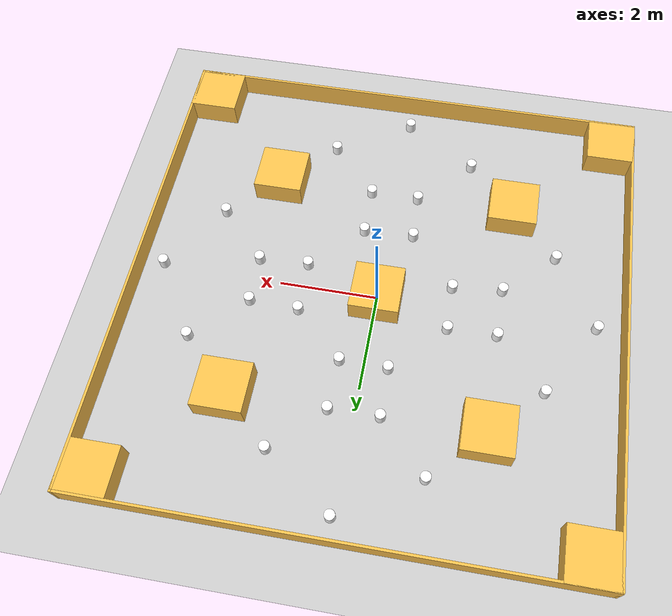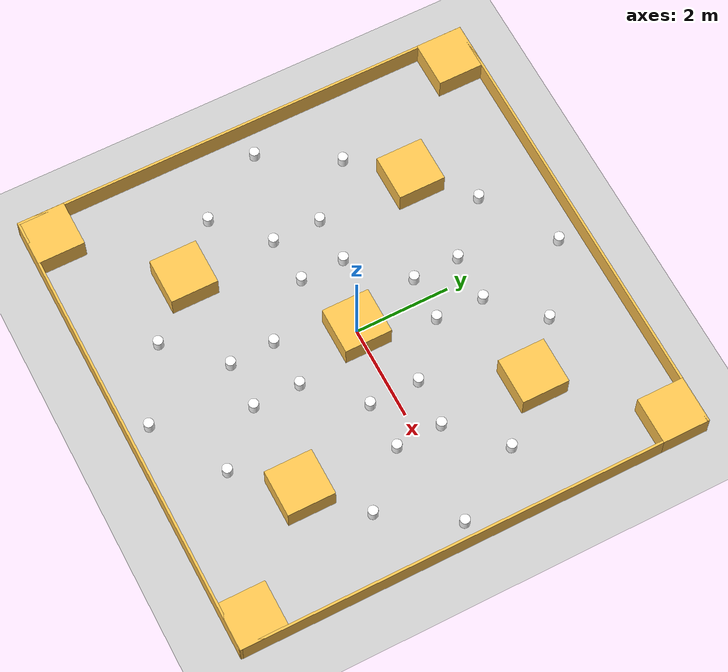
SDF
<sdf version="1.6">
 <world name="default">
  <light name="sun" type="directional">
   <pose>0 0 10 0 -0 0</pose>
   <diffuse>0.8 0.8 0.8 1</diffuse>
   <specular>0.1 0.1 0.1 1</specular>
   <attenuation>
    <range>1000</range>
    <constant>0.9</constant>
    <linear>0.01</linear>
    <quadratic>0.001</quadratic>
   </attenuation>
   <direction>-0.5 0.5 -1</direction>
  </light>
  <model name="ground_plane">
   <static>1</static>
   <link name="link">
    <collision name="collision">
     <geometry><plane><normal>0 0 1</normal><size>100 100</size></plane></geometry>
     <surface><friction><ode><mu>100</mu><mu2>50</mu2></ode></friction></surface>
    </collision>
    <visual name="visual">
     <cast_shadows>0</cast_shadows>
     <geometry><plane><normal>0 0 1</normal><size>100 100</size></plane></geometry>
     <material>
      <script><uri>file://media/materials/scripts/gazebo.material</uri><name>Gazebo/Grey</name></script>
     </material>
    </visual>
   </link>
  </model>
  <gravity>0 0 -9.8</gravity>
  <magnetic_field>6e-06 2.3e-05 -4.2e-05</magnetic_field>
  <atmosphere type="adiabatic"/>
  <physics name="default_physics" default="0" type="ode">
   <max_step_size>0.001</max_step_size>
   <real_time_factor>1</real_time_factor>
   <real_time_update_rate>1000</real_time_update_rate>
  </physics>
  <scene><ambient>0.4 0.4 0.4 1</ambient><background>0.7 0.7 0.7 1</background><shadows>1</shadows></scene>
  <spherical_coordinates>
   <surface_model>EARTH_WGS84</surface_model>
   <latitude_deg>0</latitude_deg>
   <longitude_deg>0</longitude_deg>
   <elevation>0</elevation>
   <heading_deg>0</heading_deg>
  </spherical_coordinates>
  <model name="low-map">
   <pose>-0.009415 0.0011 0 0 -0 0</pose>
   <link name="Wall_27">
    <collision name="Wall_27_Collision">
     <geometry><box><size>9.89993 0.05 0.5</size></box></geometry>
     <pose>0 0 0.25 0 -0 0</pose>
    </collision>
    <visual name="Wall_27_Visual">
     <pose>0 0 0.25 0 -0 0</pose>
     <geometry><box><size>9.89993 0.05 0.5</size></box></geometry>
     <material>
      <script><uri>file://media/materials/scripts/gazebo.material</uri><name>Gazebo/Grey</name></script>
      <ambient>1 0.764706 0.305882 1</ambient>
     </material>
    </visual>
    <pose>0 4.925 0 0 -0 0</pose>
   </link>
   <link name="Wall_28">
    <collision name="Wall_28_Collision">
     <geometry><box><size>9.90017 0.05 0.5</size></box></geometry>
     <pose>0 0 0.25 0 -0 0</pose>
    </collision>
    <visual name="Wall_28_Visual">
     <pose>0 0 0.25 0 -0 0</pose>
     <geometry><box><size>9.90017 0.05 0.5</size></box></geometry>
     <material>
      <script><uri>file://media/materials/scripts/gazebo.material</uri><name>Gazebo/Grey</name></script>
      <ambient>1 0.764706 0.305882 1</ambient>
     </material>
    </visual>
    <pose>4.925 0 0 0 0 -1.5708</pose>
   </link>
   <link name="Wall_29">
    <collision name="Wall_29_Collision">
     <geometry><box><size>9.90007 0.05 0.5</size></box></geometry>
     <pose>0 0 0.25 0 -0 0</pose>
    </collision>
    <visual name="Wall_29_Visual">
     <pose>0 0 0.25 0 -0 0</pose>
     <geometry><box><size>9.90007 0.05 0.5</size></box></geometry>
     <material>
      <script><uri>file://media/materials/scripts/gazebo.material</uri><name>Gazebo/Grey</name></script>
      <ambient>1 0.764706 0.305882 1</ambient>
     </material>
    </visual>
    <pose>0 -4.925 0 0 -0 3.14159</pose>
   </link>
   <link name="Wall_30">
    <collision name="Wall_30_Collision">
     <geometry><box><size>9.9 0.05 0.5</size></box></geometry>
     <pose>0 0 0.25 0 -0 0</pose>
    </collision>
    <visual name="Wall_30_Visual">
     <pose>0 0 0.25 0 -0 0</pose>
     <geometry><box><size>9.9 0.05 0.5</size></box></geometry>
     <material>
      <script><uri>file://media/materials/scripts/gazebo.material</uri><name>Gazebo/Grey</name></script>
      <ambient>1 0.764706 0.305882 1</ambient>
     </material>
    </visual>
    <pose>-4.925 0 0 0 -0 1.5708</pose>
   </link>
   <static>1</static>
  </model>
  <model name="unit_box_0_orange_clone_7">
   <link name="link">
    <inertial>
     <mass>10</mass>
     <inertia><ixx>0.473401</ixx><ixy>0</ixy><ixz>0</ixz><iyy>2.14637</iyy><iyz>0</iyz><izz>2.14637</izz></inertia>
    </inertial>
    <visual name="visual">
     <geometry><box><size>1.00001 1 0.5</size></box></geometry>
     <material>
      <script><name>Gazebo/Grey</name><uri>file://media/materials/scripts/gazebo.material</uri></script>
      <ambient>1 0.765 0.306 1</ambient>
      <diffuse>0.7 0.7 0.7 1</diffuse>
      <specular>0.01 0.01 0.01 1</specular>
      <emissive>0 0 0 1</emissive>
      <shader type="vertex"><normal_map>__default__</normal_map></shader>
     </material>
    </visual>
    <collision name="collision">
     <geometry><box><size>1 1 0.5</size></box></geometry>
     <surface>
      <friction>
       <ode><mu>1</mu><mu2>1</mu2><fdir1>0 0 0</fdir1><slip1>0</slip1><slip2>0</slip2></ode>
       <torsional>
        <coefficient>1</coefficient>
        <patch_radius>0</patch_radius>
        <surface_radius>0</surface_radius>
        <use_patch_radius>1</use_patch_radius>
        <ode><slip>0</slip></ode>
       </torsional>
      </friction>
      <bounce><restitution_coefficient>0</restitution_coefficient><threshold>1e+06</threshold></bounce>
      <contact>
       <collide_without_contact>0</collide_without_contact>
       <collide_without_contact_bitmask>1</collide_without_contact_bitmask>
       <collide_bitmask>1</collide_bitmask>
       <ode>
        <soft_cfm>0</soft_cfm>
        <soft_erp>0.2</soft_erp>
        <kp>1e+13</kp>
        <kd>1</kd>
        <max_vel>0.01</max_vel>
        <min_depth>0</min_depth>
       </ode>
       <bullet>
        <split_impulse>1</split_impulse>
        <split_impulse_penetration_threshold>-0.01</split_impulse_penetration_threshold>
        <soft_cfm>0</soft_cfm>
        <soft_erp>0.2</soft_erp>
        <kp>1e+13</kp>
        <kd>1</kd>
       </bullet>
      </contact>
     </surface>
    </collision>
   </link>
   <static>1</static>
   <pose>2.5 -2.5 0.25 0 -0 0</pose>
  </model>
  <model name="unit_box_0_orange_clone_8">
   <link name="link">
    <inertial>
     <mass>10</mass>
     <inertia><ixx>0.473401</ixx><ixy>0</ixy><ixz>0</ixz><iyy>2.14637</iyy><iyz>0</iyz><izz>2.14637</izz></inertia>
    </inertial>
    <visual name="visual">
     <geometry><box><size>1.00001 1 0.5</size></box></geometry>
     <material>
      <script><name>Gazebo/Grey</name><uri>file://media/materials/scripts/gazebo.material</uri></script>
      <ambient>1 0.765 0.306 1</ambient>
      <diffuse>0.7 0.7 0.7 1</diffuse>
      <specular>0.01 0.01 0.01 1</specular>
      <emissive>0 0 0 1</emissive>
      <shader type="vertex"><normal_map>__default__</normal_map></shader>
     </material>
    </visual>
    <collision name="collision">
     <geometry><box><size>1 1 0.5</size></box></geometry>
     <surface>
      <friction>
       <ode><mu>1</mu><mu2>1</mu2><fdir1>0 0 0</fdir1><slip1>0</slip1><slip2>0</slip2></ode>
       <torsional>
        <coefficient>1</coefficient>
        <patch_radius>0</patch_radius>
        <surface_radius>0</surface_radius>
        <use_patch_radius>1</use_patch_radius>
        <ode><slip>0</slip></ode>
       </torsional>
      </friction>
      <bounce><restitution_coefficient>0</restitution_coefficient><threshold>1e+06</threshold></bounce>
      <contact>
       <collide_without_contact>0</collide_without_contact>
       <collide_without_contact_bitmask>1</collide_without_contact_bitmask>
       <collide_bitmask>1</collide_bitmask>
       <ode>
        <soft_cfm>0</soft_cfm>
        <soft_erp>0.2</soft_erp>
        <kp>1e+13</kp>
        <kd>1</kd>
        <max_vel>0.01</max_vel>
        <min_depth>0</min_depth>
       </ode>
       <bullet>
        <split_impulse>1</split_impulse>
        <split_impulse_penetration_threshold>-0.01</split_impulse_penetration_threshold>
        <soft_cfm>0</soft_cfm>
        <soft_erp>0.2</soft_erp>
        <kp>1e+13</kp>
        <kd>1</kd>
       </bullet>
      </contact>
     </surface>
    </collision>
   </link>
   <static>1</static>
   <pose>-2.5 -2.5 0.25 0 -0 0</pose>
  </model>
  <model name="unit_box_0_orange_clone_8_clone">
   <link name="link">
    <inertial>
     <mass>10</mass>
     <inertia><ixx>0.473401</ixx><ixy>0</ixy><ixz>0</ixz><iyy>2.14637</iyy><iyz>0</iyz><izz>2.14637</izz></inertia>
    </inertial>
    <visual name="visual">
     <geometry><box><size>1.00001 1 0.5</size></box></geometry>
     <material>
      <script><name>Gazebo/Grey</name><uri>file://media/materials/scripts/gazebo.material</uri></script>
      <ambient>1 0.765 0.306 1</ambient>
      <diffuse>0.7 0.7 0.7 1</diffuse>
      <specular>0.01 0.01 0.01 1</specular>
      <emissive>0 0 0 1</emissive>
      <shader type="vertex"><normal_map>__default__</normal_map></shader>
     </material>
    </visual>
    <collision name="collision">
     <geometry><box><size>1 1 0.5</size></box></geometry>
     <surface>
      <friction>
       <ode><mu>1</mu><mu2>1</mu2><fdir1>0 0 0</fdir1><slip1>0</slip1><slip2>0</slip2></ode>
       <torsional>
        <coefficient>1</coefficient>
        <patch_radius>0</patch_radius>
        <surface_radius>0</surface_radius>
        <use_patch_radius>1</use_patch_radius>
        <ode><slip>0</slip></ode>
       </torsional>
      </friction>
      <bounce><restitution_coefficient>0</restitution_coefficient><threshold>1e+06</threshold></bounce>
      <contact>
       <collide_without_contact>0</collide_without_contact>
       <collide_without_contact_bitmask>1</collide_without_contact_bitmask>
       <collide_bitmask>1</collide_bitmask>
       <ode>
        <soft_cfm>0</soft_cfm>
        <soft_erp>0.2</soft_erp>
        <kp>1e+13</kp>
        <kd>1</kd>
        <max_vel>0.01</max_vel>
        <min_depth>0</min_depth>
       </ode>
       <bullet>
        <split_impulse>1</split_impulse>
        <split_impulse_penetration_threshold>-0.01</split_impulse_penetration_threshold>
        <soft_cfm>0</soft_cfm>
        <soft_erp>0.2</soft_erp>
        <kp>1e+13</kp>
        <kd>1</kd>
       </bullet>
      </contact>
     </surface>
    </collision>
   </link>
   <static>1</static>
   <pose>-2.5 2.5 0.25 0 -0 0</pose>
  </model>
  <model name="unit_box_0_orange_clone_8_clone_0">
   <link name="link">
    <inertial>
     <mass>10</mass>
     <inertia><ixx>0.473401</ixx><ixy>0</ixy><ixz>0</ixz><iyy>2.14637</iyy><iyz>0</iyz><izz>2.14637</izz></inertia>
    </inertial>
    <visual name="visual">
     <geometry><box><size>1.00001 1 0.5</size></box></geometry>
     <material>
      <script><name>Gazebo/Grey</name><uri>file://media/materials/scripts/gazebo.material</uri></script>
      <ambient>1 0.765 0.306 1</ambient>
      <diffuse>0.7 0.7 0.7 1</diffuse>
      <specular>0.01 0.01 0.01 1</specular>
      <emissive>0 0 0 1</emissive>
      <shader type="vertex"><normal_map>__default__</normal_map></shader>
     </material>
    </visual>
    <collision name="collision">
     <geometry><box><size>1 1 0.5</size></box></geometry>
     <surface>
      <friction>
       <ode><mu>1</mu><mu2>1</mu2><fdir1>0 0 0</fdir1><slip1>0</slip1><slip2>0</slip2></ode>
       <torsional>
        <coefficient>1</coefficient>
        <patch_radius>0</patch_radius>
        <surface_radius>0</surface_radius>
        <use_patch_radius>1</use_patch_radius>
        <ode><slip>0</slip></ode>
       </torsional>
      </friction>
      <bounce><restitution_coefficient>0</restitution_coefficient><threshold>1e+06</threshold></bounce>
      <contact>
       <collide_without_contact>0</collide_without_contact>
       <collide_without_contact_bitmask>1</collide_without_contact_bitmask>
       <collide_bitmask>1</collide_bitmask>
       <ode>
        <soft_cfm>0</soft_cfm>
        <soft_erp>0.2</soft_erp>
        <kp>1e+13</kp>
        <kd>1</kd>
        <max_vel>0.01</max_vel>
        <min_depth>0</min_depth>
       </ode>
       <bullet>
        <split_impulse>1</split_impulse>
        <split_impulse_penetration_threshold>-0.01</split_impulse_penetration_threshold>
        <soft_cfm>0</soft_cfm>
        <soft_erp>0.2</soft_erp>
        <kp>1e+13</kp>
        <kd>1</kd>
       </bullet>
      </contact>
     </surface>
    </collision>
   </link>
   <static>1</static>
   <pose>2.5 2.5 0.25 0 -0 0</pose>
  </model>
  <model name="unit_box_0_orange_clone_8_clone_1">
   <link name="link">
    <inertial>
     <mass>10</mass>
     <inertia><ixx>0.473401</ixx><ixy>0</ixy><ixz>0</ixz><iyy>2.14637</iyy><iyz>0</iyz><izz>2.14637</izz></inertia>
    </inertial>
    <visual name="visual">
     <geometry><box><size>1.00001 1 0.5</size></box></geometry>
     <material>
      <script><name>Gazebo/Grey</name><uri>file://media/materials/scripts/gazebo.material</uri></script>
      <ambient>1 0.765 0.306 1</ambient>
      <diffuse>0.7 0.7 0.7 1</diffuse>
      <specular>0.01 0.01 0.01 1</specular>
      <emissive>0 0 0 1</emissive>
      <shader type="vertex"><normal_map>__default__</normal_map></shader>
     </material>
    </visual>
    <collision name="collision">
     <geometry><box><size>1 1 0.5</size></box></geometry>
     <surface>
      <friction>
       <ode><mu>1</mu><mu2>1</mu2><fdir1>0 0 0</fdir1><slip1>0</slip1><slip2>0</slip2></ode>
       <torsional>
        <coefficient>1</coefficient>
        <patch_radius>0</patch_radius>
        <surface_radius>0</surface_radius>
        <use_patch_radius>1</use_patch_radius>
        <ode><slip>0</slip></ode>
       </torsional>
      </friction>
      <bounce><restitution_coefficient>0</restitution_coefficient><threshold>1e+06</threshold></bounce>
      <contact>
       <collide_without_contact>0</collide_without_contact>
       <collide_without_contact_bitmask>1</collide_without_contact_bitmask>
       <collide_bitmask>1</collide_bitmask>
       <ode>
        <soft_cfm>0</soft_cfm>
        <soft_erp>0.2</soft_erp>
        <kp>1e+13</kp>
        <kd>1</kd>
        <max_vel>0.01</max_vel>
        <min_depth>0</min_depth>
       </ode>
       <bullet>
        <split_impulse>1</split_impulse>
        <split_impulse_penetration_threshold>-0.01</split_impulse_penetration_threshold>
        <soft_cfm>0</soft_cfm>
        <soft_erp>0.2</soft_erp>
        <kp>1e+13</kp>
        <kd>1</kd>
       </bullet>
      </contact>
     </surface>
    </collision>
   </link>
   <static>1</static>
   <pose>0 0 0.25 0 -0 0</pose>
  </model>
  <model name="unit_box_0_orange_clone_7_clone">
   <link name="link">
    <inertial>
     <mass>10</mass>
     <inertia><ixx>0.473401</ixx><ixy>0</ixy><ixz>0</ixz><iyy>2.14637</iyy><iyz>0</iyz><izz>2.14637</izz></inertia>
    </inertial>
    <visual name="visual">
     <geometry><box><size>1.00001 1 0.5</size></box></geometry>
     <material>
      <script><name>Gazebo/Grey</name><uri>file://media/materials/scripts/gazebo.material</uri></script>
      <ambient>1 0.765 0.306 1</ambient>
      <diffuse>0.7 0.7 0.7 1</diffuse>
      <specular>0.01 0.01 0.01 1</specular>
      <emissive>0 0 0 1</emissive>
      <shader type="vertex"><normal_map>__default__</normal_map></shader>
     </material>
    </visual>
    <collision name="collision">
     <geometry><box><size>1 1 0.5</size></box></geometry>
     <surface>
      <friction>
       <ode><mu>1</mu><mu2>1</mu2><fdir1>0 0 0</fdir1><slip1>0</slip1><slip2>0</slip2></ode>
       <torsional>
        <coefficient>1</coefficient>
        <patch_radius>0</patch_radius>
        <surface_radius>0</surface_radius>
        <use_patch_radius>1</use_patch_radius>
        <ode><slip>0</slip></ode>
       </torsional>
      </friction>
      <bounce><restitution_coefficient>0</restitution_coefficient><threshold>1e+06</threshold></bounce>
      <contact>
       <collide_without_contact>0</collide_without_contact>
       <collide_without_contact_bitmask>1</collide_without_contact_bitmask>
       <collide_bitmask>1</collide_bitmask>
       <ode>
        <soft_cfm>0</soft_cfm>
        <soft_erp>0.2</soft_erp>
        <kp>1e+13</kp>
        <kd>1</kd>
        <max_vel>0.01</max_vel>
        <min_depth>0</min_depth>
       </ode>
       <bullet>
        <split_impulse>1</split_impulse>
        <split_impulse_penetration_threshold>-0.01</split_impulse_penetration_threshold>
        <soft_cfm>0</soft_cfm>
        <soft_erp>0.2</soft_erp>
        <kp>1e+13</kp>
        <kd>1</kd>
       </bullet>
      </contact>
     </surface>
    </collision>
   </link>
   <static>1</static>
   <pose>4.43771 -4.44352 0.25 0 -0 0</pose>
  </model>
  <model name="unit_box_0_orange_clone_7_clone_0">
   <link name="link">
    <inertial>
     <mass>10</mass>
     <inertia><ixx>0.473401</ixx><ixy>0</ixy><ixz>0</ixz><iyy>2.14637</iyy><iyz>0</iyz><izz>2.14637</izz></inertia>
    </inertial>
    <visual name="visual">
     <geometry><box><size>1.00001 1 0.5</size></box></geometry>
     <material>
      <script><name>Gazebo/Grey</name><uri>file://media/materials/scripts/gazebo.material</uri></script>
      <ambient>1 0.765 0.306 1</ambient>
      <diffuse>0.7 0.7 0.7 1</diffuse>
      <specular>0.01 0.01 0.01 1</specular>
      <emissive>0 0 0 1</emissive>
      <shader type="vertex"><normal_map>__default__</normal_map></shader>
     </material>
    </visual>
    <collision name="collision">
     <geometry><box><size>1 1 0.5</size></box></geometry>
     <surface>
      <friction>
       <ode><mu>1</mu><mu2>1</mu2><fdir1>0 0 0</fdir1><slip1>0</slip1><slip2>0</slip2></ode>
       <torsional>
        <coefficient>1</coefficient>
        <patch_radius>0</patch_radius>
        <surface_radius>0</surface_radius>
        <use_patch_radius>1</use_patch_radius>
        <ode><slip>0</slip></ode>
       </torsional>
      </friction>
      <bounce><restitution_coefficient>0</restitution_coefficient><threshold>1e+06</threshold></bounce>
      <contact>
       <collide_without_contact>0</collide_without_contact>
       <collide_without_contact_bitmask>1</collide_without_contact_bitmask>
       <collide_bitmask>1</collide_bitmask>
       <ode>
        <soft_cfm>0</soft_cfm>
        <soft_erp>0.2</soft_erp>
        <kp>1e+13</kp>
        <kd>1</kd>
        <max_vel>0.01</max_vel>
        <min_depth>0</min_depth>
       </ode>
       <bullet>
        <split_impulse>1</split_impulse>
        <split_impulse_penetration_threshold>-0.01</split_impulse_penetration_threshold>
        <soft_cfm>0</soft_cfm>
        <soft_erp>0.2</soft_erp>
        <kp>1e+13</kp>
        <kd>1</kd>
       </bullet>
      </contact>
     </surface>
    </collision>
   </link>
   <static>1</static>
   <pose>-4.45682 -4.44621 0.25 0 -0 0</pose>
  </model>
  <model name="unit_box_0_orange_clone_7_clone_1">
   <link name="link">
    <inertial>
     <mass>10</mass>
     <inertia><ixx>0.473401</ixx><ixy>0</ixy><ixz>0</ixz><iyy>2.14637</iyy><iyz>0</iyz><izz>2.14637</izz></inertia>
    </inertial>
    <visual name="visual">
     <geometry><box><size>1.00001 1 0.5</size></box></geometry>
     <material>
      <script><name>Gazebo/Grey</name><uri>file://media/materials/scripts/gazebo.material</uri></script>
      <ambient>1 0.765 0.306 1</ambient>
      <diffuse>0.7 0.7 0.7 1</diffuse>
      <specular>0.01 0.01 0.01 1</specular>
      <emissive>0 0 0 1</emissive>
      <shader type="vertex"><normal_map>__default__</normal_map></shader>
     </material>
    </visual>
    <collision name="collision">
     <geometry><box><size>1 1 0.5</size></box></geometry>
     <surface>
      <friction>
       <ode><mu>1</mu><mu2>1</mu2><fdir1>0 0 0</fdir1><slip1>0</slip1><slip2>0</slip2></ode>
       <torsional>
        <coefficient>1</coefficient>
        <patch_radius>0</patch_radius>
        <surface_radius>0</surface_radius>
        <use_patch_radius>1</use_patch_radius>
        <ode><slip>0</slip></ode>
       </torsional>
      </friction>
      <bounce><restitution_coefficient>0</restitution_coefficient><threshold>1e+06</threshold></bounce>
      <contact>
       <collide_without_contact>0</collide_without_contact>
       <collide_without_contact_bitmask>1</collide_without_contact_bitmask>
       <collide_bitmask>1</collide_bitmask>
       <ode>
        <soft_cfm>0</soft_cfm>
        <soft_erp>0.2</soft_erp>
        <kp>1e+13</kp>
        <kd>1</kd>
        <max_vel>0.01</max_vel>
        <min_depth>0</min_depth>
       </ode>
       <bullet>
        <split_impulse>1</split_impulse>
        <split_impulse_penetration_threshold>-0.01</split_impulse_penetration_threshold>
        <soft_cfm>0</soft_cfm>
        <soft_erp>0.2</soft_erp>
        <kp>1e+13</kp>
        <kd>1</kd>
       </bullet>
      </contact>
     </surface>
    </collision>
   </link>
   <static>1</static>
   <pose>-4.4589 4.44936 0.25 0 -0 0</pose>
  </model>
  <model name="unit_box_0_orange_clone_7_clone_2">
   <link name="link">
    <inertial>
     <mass>10</mass>
     <inertia><ixx>0.473401</ixx><ixy>0</ixy><ixz>0</ixz><iyy>2.14637</iyy><iyz>0</iyz><izz>2.14637</izz></inertia>
    </inertial>
    <visual name="visual">
     <geometry><box><size>1.00001 1 0.5</size></box></geometry>
     <material>
      <script><name>Gazebo/Grey</name><uri>file://media/materials/scripts/gazebo.material</uri></script>
      <ambient>1 0.765 0.306 1</ambient>
      <diffuse>0.7 0.7 0.7 1</diffuse>
      <specular>0.01 0.01 0.01 1</specular>
      <emissive>0 0 0 1</emissive>
      <shader type="vertex"><normal_map>__default__</normal_map></shader>
     </material>
    </visual>
    <collision name="collision">
     <geometry><box><size>1 1 0.5</size></box></geometry>
     <surface>
      <friction>
       <ode><mu>1</mu><mu2>1</mu2><fdir1>0 0 0</fdir1><slip1>0</slip1><slip2>0</slip2></ode>
       <torsional>
        <coefficient>1</coefficient>
        <patch_radius>0</patch_radius>
        <surface_radius>0</surface_radius>
        <use_patch_radius>1</use_patch_radius>
        <ode><slip>0</slip></ode>
       </torsional>
      </friction>
      <bounce><restitution_coefficient>0</restitution_coefficient><threshold>1e+06</threshold></bounce>
      <contact>
       <collide_without_contact>0</collide_without_contact>
       <collide_without_contact_bitmask>1</collide_without_contact_bitmask>
       <collide_bitmask>1</collide_bitmask>
       <ode>
        <soft_cfm>0</soft_cfm>
        <soft_erp>0.2</soft_erp>
        <kp>1e+13</kp>
        <kd>1</kd>
        <max_vel>0.01</max_vel>
        <min_depth>0</min_depth>
       </ode>
       <bullet>
        <split_impulse>1</split_impulse>
        <split_impulse_penetration_threshold>-0.01</split_impulse_penetration_threshold>
        <soft_cfm>0</soft_cfm>
        <soft_erp>0.2</soft_erp>
        <kp>1e+13</kp>
        <kd>1</kd>
       </bullet>
      </contact>
     </surface>
    </collision>
   </link>
   <static>1</static>
   <pose>4.44066 4.44748 0.25 0 -0 0</pose>
  </model>
  <model name="beer_big_0">
   <link name="link">
    <pose>0 0 0.115 0 -0 0</pose>
    <inertial>
     <mass>1.34731</mass>
     <inertia>
      <ixx>0.0028093</ixx>
      <ixy>0</ixy>
      <ixz>0</ixz>
      <iyy>0.0028093</iyy>
      <iyz>0</iyz>
      <izz>0.00226756</izz>
     </inertia>
    </inertial>
    <visual name="visual">
     <geometry><cylinder><radius>0.102222</radius><length>0.23</length></cylinder></geometry>
     <material>
      <script>
       <uri>model://beer/materials/scripts</uri>
       <uri>model://beer/materials/textures</uri>
       <name>Beer/Diffuse</name>
      </script>
      <ambient>1 1 1 1</ambient>
      <diffuse>1 1 1 1</diffuse>
      <specular>0 0 0 1</specular>
      <emissive>0 0 0 1</emissive>
     </material>
    </visual>
    <collision name="collision">
     <geometry><cylinder><radius>0.102222</radius><length>0.23</length></cylinder></geometry>
     <surface>
      <friction>
       <ode><mu>1</mu><mu2>1</mu2><fdir1>0 0 0</fdir1><slip1>0</slip1><slip2>0</slip2></ode>
       <torsional>
        <coefficient>1</coefficient>
        <patch_radius>0</patch_radius>
        <surface_radius>0</surface_radius>
        <use_patch_radius>1</use_patch_radius>
        <ode><slip>0</slip></ode>
       </torsional>
      </friction>
      <bounce><restitution_coefficient>0</restitution_coefficient><threshold>1e+06</threshold></bounce>
      <contact>
       <collide_without_contact>0</collide_without_contact>
       <collide_without_contact_bitmask>1</collide_without_contact_bitmask>
       <collide_bitmask>1</collide_bitmask>
       <ode>
        <soft_cfm>0</soft_cfm>
        <soft_erp>0.2</soft_erp>
        <kp>1e+13</kp>
        <kd>1</kd>
        <max_vel>0.01</max_vel>
        <min_depth>0</min_depth>
       </ode>
       <bullet>
        <split_impulse>1</split_impulse>
        <split_impulse_penetration_threshold>-0.01</split_impulse_penetration_threshold>
        <soft_cfm>0</soft_cfm>
        <soft_erp>0.2</soft_erp>
        <kp>1e+13</kp>
        <kd>1</kd>
       </bullet>
      </contact>
     </surface>
    </collision>
   </link>
   <static>0</static>
   <pose>4.47702 -0.049065 0 0 0 -5e-06</pose>
  </model>
  <model name="beer_big_1">
   <link name="link">
    <pose>0 0 0.115 0 -0 0</pose>
    <inertial>
     <mass>1.34731</mass>
     <inertia>
      <ixx>0.0028093</ixx>
      <ixy>0</ixy>
      <ixz>0</ixz>
      <iyy>0.0028093</iyy>
      <iyz>0</iyz>
      <izz>0.00226756</izz>
     </inertia>
    </inertial>
    <visual name="visual">
     <geometry><cylinder><radius>0.102222</radius><length>0.23</length></cylinder></geometry>
     <material>
      <script>
       <uri>model://beer/materials/scripts</uri>
       <uri>model://beer/materials/textures</uri>
       <name>Beer/Diffuse</name>
      </script>
      <ambient>1 1 1 1</ambient>
      <diffuse>1 1 1 1</diffuse>
      <specular>0 0 0 1</specular>
      <emissive>0 0 0 1</emissive>
     </material>
    </visual>
    <collision name="collision">
     <geometry><cylinder><radius>0.102222</radius><length>0.23</length></cylinder></geometry>
     <surface>
      <friction>
       <ode><mu>1</mu><mu2>1</mu2><fdir1>0 0 0</fdir1><slip1>0</slip1><slip2>0</slip2></ode>
       <torsional>
        <coefficient>1</coefficient>
        <patch_radius>0</patch_radius>
        <surface_radius>0</surface_radius>
        <use_patch_radius>1</use_patch_radius>
        <ode><slip>0</slip></ode>
       </torsional>
      </friction>
      <bounce><restitution_coefficient>0</restitution_coefficient><threshold>1e+06</threshold></bounce>
      <contact>
       <collide_without_contact>0</collide_without_contact>
       <collide_without_contact_bitmask>1</collide_without_contact_bitmask>
       <collide_bitmask>1</collide_bitmask>
       <ode>
        <soft_cfm>0</soft_cfm>
        <soft_erp>0.2</soft_erp>
        <kp>1e+13</kp>
        <kd>1</kd>
        <max_vel>0.01</max_vel>
        <min_depth>0</min_depth>
       </ode>
       <bullet>
        <split_impulse>1</split_impulse>
        <split_impulse_penetration_threshold>-0.01</split_impulse_penetration_threshold>
        <soft_cfm>0</soft_cfm>
        <soft_erp>0.2</soft_erp>
        <kp>1e+13</kp>
        <kd>1</kd>
       </bullet>
      </contact>
     </surface>
    </collision>
   </link>
   <static>0</static>
   <pose>3.52895 -1.49271 0 0 -0 0</pose>
  </model>
  <model name="beer_big_2">
   <link name="link">
    <pose>0 0 0.115 0 -0 0</pose>
    <inertial>
     <mass>1.34731</mass>
     <inertia>
      <ixx>0.0028093</ixx>
      <ixy>0</ixy>
      <ixz>0</ixz>
      <iyy>0.0028093</iyy>
      <iyz>0</iyz>
      <izz>0.00226756</izz>
     </inertia>
    </inertial>
    <visual name="visual">
     <geometry><cylinder><radius>0.102222</radius><length>0.23</length></cylinder></geometry>
     <material>
      <script>
       <uri>model://beer/materials/scripts</uri>
       <uri>model://beer/materials/textures</uri>
       <name>Beer/Diffuse</name>
      </script>
      <ambient>1 1 1 1</ambient>
      <diffuse>1 1 1 1</diffuse>
      <specular>0 0 0 1</specular>
      <emissive>0 0 0 1</emissive>
     </material>
    </visual>
    <collision name="collision">
     <geometry><cylinder><radius>0.102222</radius><length>0.23</length></cylinder></geometry>
     <surface>
      <friction>
       <ode><mu>1</mu><mu2>1</mu2><fdir1>0 0 0</fdir1><slip1>0</slip1><slip2>0</slip2></ode>
       <torsional>
        <coefficient>1</coefficient>
        <patch_radius>0</patch_radius>
        <surface_radius>0</surface_radius>
        <use_patch_radius>1</use_patch_radius>
        <ode><slip>0</slip></ode>
       </torsional>
      </friction>
      <bounce><restitution_coefficient>0</restitution_coefficient><threshold>1e+06</threshold></bounce>
      <contact>
       <collide_without_contact>0</collide_without_contact>
       <collide_without_contact_bitmask>1</collide_without_contact_bitmask>
       <collide_bitmask>1</collide_bitmask>
       <ode>
        <soft_cfm>0</soft_cfm>
        <soft_erp>0.2</soft_erp>
        <kp>1e+13</kp>
        <kd>1</kd>
        <max_vel>0.01</max_vel>
        <min_depth>0</min_depth>
       </ode>
       <bullet>
        <split_impulse>1</split_impulse>
        <split_impulse_penetration_threshold>-0.01</split_impulse_penetration_threshold>
        <soft_cfm>0</soft_cfm>
        <soft_erp>0.2</soft_erp>
        <kp>1e+13</kp>
        <kd>1</kd>
       </bullet>
      </contact>
     </surface>
    </collision>
   </link>
   <static>0</static>
   <pose>3.53977 1.47202 0 0 -0 0</pose>
  </model>
  <model name="beer_big_3">
   <link name="link">
    <pose>0 0 0.115 0 -0 0</pose>
    <inertial>
     <mass>1.34731</mass>
     <inertia>
      <ixx>0.0028093</ixx>
      <ixy>0</ixy>
      <ixz>0</ixz>
      <iyy>0.0028093</iyy>
      <iyz>0</iyz>
      <izz>0.00226756</izz>
     </inertia>
    </inertial>
    <visual name="visual">
     <geometry><cylinder><radius>0.102222</radius><length>0.23</length></cylinder></geometry>
     <material>
      <script>
       <uri>model://beer/materials/scripts</uri>
       <uri>model://beer/materials/textures</uri>
       <name>Beer/Diffuse</name>
      </script>
      <ambient>1 1 1 1</ambient>
      <diffuse>1 1 1 1</diffuse>
      <specular>0 0 0 1</specular>
      <emissive>0 0 0 1</emissive>
     </material>
    </visual>
    <collision name="collision">
     <geometry><cylinder><radius>0.102222</radius><length>0.23</length></cylinder></geometry>
     <surface>
      <friction>
       <ode><mu>1</mu><mu2>1</mu2><fdir1>0 0 0</fdir1><slip1>0</slip1><slip2>0</slip2></ode>
       <torsional>
        <coefficient>1</coefficient>
        <patch_radius>0</patch_radius>
        <surface_radius>0</surface_radius>
        <use_patch_radius>1</use_patch_radius>
        <ode><slip>0</slip></ode>
       </torsional>
      </friction>
      <bounce><restitution_coefficient>0</restitution_coefficient><threshold>1e+06</threshold></bounce>
      <contact>
       <collide_without_contact>0</collide_without_contact>
       <collide_without_contact_bitmask>1</collide_without_contact_bitmask>
       <collide_bitmask>1</collide_bitmask>
       <ode>
        <soft_cfm>0</soft_cfm>
        <soft_erp>0.2</soft_erp>
        <kp>1e+13</kp>
        <kd>1</kd>
        <max_vel>0.01</max_vel>
        <min_depth>0</min_depth>
       </ode>
       <bullet>
        <split_impulse>1</split_impulse>
        <split_impulse_penetration_threshold>-0.01</split_impulse_penetration_threshold>
        <soft_cfm>0</soft_cfm>
        <soft_erp>0.2</soft_erp>
        <kp>1e+13</kp>
        <kd>1</kd>
       </bullet>
      </contact>
     </surface>
    </collision>
   </link>
   <static>0</static>
   <pose>2.5427 -0.464399 0 0 -0 0</pose>
  </model>
  <model name="beer_big_4">
   <link name="link">
    <pose>0 0 0.115 0 -0 0</pose>
    <inertial>
     <mass>1.34731</mass>
     <inertia>
      <ixx>0.0028093</ixx>
      <ixy>0</ixy>
      <ixz>0</ixz>
      <iyy>0.0028093</iyy>
      <iyz>0</iyz>
      <izz>0.00226756</izz>
     </inertia>
    </inertial>
    <visual name="visual">
     <geometry><cylinder><radius>0.102222</radius><length>0.23</length></cylinder></geometry>
     <material>
      <script>
       <uri>model://beer/materials/scripts</uri>
       <uri>model://beer/materials/textures</uri>
       <name>Beer/Diffuse</name>
      </script>
      <ambient>1 1 1 1</ambient>
      <diffuse>1 1 1 1</diffuse>
      <specular>0 0 0 1</specular>
      <emissive>0 0 0 1</emissive>
     </material>
    </visual>
    <collision name="collision">
     <geometry><cylinder><radius>0.102222</radius><length>0.23</length></cylinder></geometry>
     <surface>
      <friction>
       <ode><mu>1</mu><mu2>1</mu2><fdir1>0 0 0</fdir1><slip1>0</slip1><slip2>0</slip2></ode>
       <torsional>
        <coefficient>1</coefficient>
        <patch_radius>0</patch_radius>
        <surface_radius>0</surface_radius>
        <use_patch_radius>1</use_patch_radius>
        <ode><slip>0</slip></ode>
       </torsional>
      </friction>
      <bounce><restitution_coefficient>0</restitution_coefficient><threshold>1e+06</threshold></bounce>
      <contact>
       <collide_without_contact>0</collide_without_contact>
       <collide_without_contact_bitmask>1</collide_without_contact_bitmask>
       <collide_bitmask>1</collide_bitmask>
       <ode>
        <soft_cfm>0</soft_cfm>
        <soft_erp>0.2</soft_erp>
        <kp>1e+13</kp>
        <kd>1</kd>
        <max_vel>0.01</max_vel>
        <min_depth>0</min_depth>
       </ode>
       <bullet>
        <split_impulse>1</split_impulse>
        <split_impulse_penetration_threshold>-0.01</split_impulse_penetration_threshold>
        <soft_cfm>0</soft_cfm>
        <soft_erp>0.2</soft_erp>
        <kp>1e+13</kp>
        <kd>1</kd>
       </bullet>
      </contact>
     </surface>
    </collision>
   </link>
   <static>0</static>
   <pose>2.52241 0.503922 0 0 -0 0</pose>
  </model>
  <model name="beer_big_5">
   <link name="link">
    <pose>0 0 0.115 0 -0 0</pose>
    <inertial>
     <mass>1.34731</mass>
     <inertia>
      <ixx>0.0028093</ixx>
      <ixy>0</ixy>
      <ixz>0</ixz>
      <iyy>0.0028093</iyy>
      <iyz>0</iyz>
      <izz>0.00226756</izz>
     </inertia>
    </inertial>
    <visual name="visual">
     <geometry><cylinder><radius>0.102222</radius><length>0.23</length></cylinder></geometry>
     <material>
      <script>
       <uri>model://beer/materials/scripts</uri>
       <uri>model://beer/materials/textures</uri>
       <name>Beer/Diffuse</name>
      </script>
      <ambient>1 1 1 1</ambient>
      <diffuse>1 1 1 1</diffuse>
      <specular>0 0 0 1</specular>
      <emissive>0 0 0 1</emissive>
     </material>
    </visual>
    <collision name="collision">
     <geometry><cylinder><radius>0.102222</radius><length>0.23</length></cylinder></geometry>
     <surface>
      <friction>
       <ode><mu>1</mu><mu2>1</mu2><fdir1>0 0 0</fdir1><slip1>0</slip1><slip2>0</slip2></ode>
       <torsional>
        <coefficient>1</coefficient>
        <patch_radius>0</patch_radius>
        <surface_radius>0</surface_radius>
        <use_patch_radius>1</use_patch_radius>
        <ode><slip>0</slip></ode>
       </torsional>
      </friction>
      <bounce><restitution_coefficient>0</restitution_coefficient><threshold>1e+06</threshold></bounce>
      <contact>
       <collide_without_contact>0</collide_without_contact>
       <collide_without_contact_bitmask>1</collide_without_contact_bitmask>
       <collide_bitmask>1</collide_bitmask>
       <ode>
        <soft_cfm>0</soft_cfm>
        <soft_erp>0.2</soft_erp>
        <kp>1e+13</kp>
        <kd>1</kd>
        <max_vel>0.01</max_vel>
        <min_depth>0</min_depth>
       </ode>
       <bullet>
        <split_impulse>1</split_impulse>
        <split_impulse_penetration_threshold>-0.01</split_impulse_penetration_threshold>
        <soft_cfm>0</soft_cfm>
        <soft_erp>0.2</soft_erp>
        <kp>1e+13</kp>
        <kd>1</kd>
       </bullet>
      </contact>
     </surface>
    </collision>
   </link>
   <static>0</static>
   <pose>1.52598 -0.504635 0 0 -0 0</pose>
  </model>
  <model name="beer_big_6">
   <link name="link">
    <pose>0 0 0.115 0 -0 0</pose>
    <inertial>
     <mass>1.34731</mass>
     <inertia>
      <ixx>0.0028093</ixx>
      <ixy>0</ixy>
      <ixz>0</ixz>
      <iyy>0.0028093</iyy>
      <iyz>0</iyz>
      <izz>0.00226756</izz>
     </inertia>
    </inertial>
    <visual name="visual">
     <geometry><cylinder><radius>0.102222</radius><length>0.23</length></cylinder></geometry>
     <material>
      <script>
       <uri>model://beer/materials/scripts</uri>
       <uri>model://beer/materials/textures</uri>
       <name>Beer/Diffuse</name>
      </script>
      <ambient>1 1 1 1</ambient>
      <diffuse>1 1 1 1</diffuse>
      <specular>0 0 0 1</specular>
      <emissive>0 0 0 1</emissive>
     </material>
    </visual>
    <collision name="collision">
     <geometry><cylinder><radius>0.102222</radius><length>0.23</length></cylinder></geometry>
     <surface>
      <friction>
       <ode><mu>1</mu><mu2>1</mu2><fdir1>0 0 0</fdir1><slip1>0</slip1><slip2>0</slip2></ode>
       <torsional>
        <coefficient>1</coefficient>
        <patch_radius>0</patch_radius>
        <surface_radius>0</surface_radius>
        <use_patch_radius>1</use_patch_radius>
        <ode><slip>0</slip></ode>
       </torsional>
      </friction>
      <bounce><restitution_coefficient>0</restitution_coefficient><threshold>1e+06</threshold></bounce>
      <contact>
       <collide_without_contact>0</collide_without_contact>
       <collide_without_contact_bitmask>1</collide_without_contact_bitmask>
       <collide_bitmask>1</collide_bitmask>
       <ode>
        <soft_cfm>0</soft_cfm>
        <soft_erp>0.2</soft_erp>
        <kp>1e+13</kp>
        <kd>1</kd>
        <max_vel>0.01</max_vel>
        <min_depth>0</min_depth>
       </ode>
       <bullet>
        <split_impulse>1</split_impulse>
        <split_impulse_penetration_threshold>-0.01</split_impulse_penetration_threshold>
        <soft_cfm>0</soft_cfm>
        <soft_erp>0.2</soft_erp>
        <kp>1e+13</kp>
        <kd>1</kd>
       </bullet>
      </contact>
     </surface>
    </collision>
   </link>
   <static>0</static>
   <pose>1.51069 0.547359 0 0 -0 0</pose>
  </model>
  <model name="beer_big_7">
   <link name="link">
    <pose>0 0 0.115 0 -0 0</pose>
    <inertial>
     <mass>1.34731</mass>
     <inertia>
      <ixx>0.0028093</ixx>
      <ixy>0</ixy>
      <ixz>0</ixz>
      <iyy>0.0028093</iyy>
      <iyz>0</iyz>
      <izz>0.00226756</izz>
     </inertia>
    </inertial>
    <visual name="visual">
     <geometry><cylinder><radius>0.102222</radius><length>0.23</length></cylinder></geometry>
     <material>
      <script>
       <uri>model://beer/materials/scripts</uri>
       <uri>model://beer/materials/textures</uri>
       <name>Beer/Diffuse</name>
      </script>
      <ambient>1 1 1 1</ambient>
      <diffuse>1 1 1 1</diffuse>
      <specular>0 0 0 1</specular>
      <emissive>0 0 0 1</emissive>
     </material>
    </visual>
    <collision name="collision">
     <geometry><cylinder><radius>0.102222</radius><length>0.23</length></cylinder></geometry>
     <surface>
      <friction>
       <ode><mu>1</mu><mu2>1</mu2><fdir1>0 0 0</fdir1><slip1>0</slip1><slip2>0</slip2></ode>
       <torsional>
        <coefficient>1</coefficient>
        <patch_radius>0</patch_radius>
        <surface_radius>0</surface_radius>
        <use_patch_radius>1</use_patch_radius>
        <ode><slip>0</slip></ode>
       </torsional>
      </friction>
      <bounce><restitution_coefficient>0</restitution_coefficient><threshold>1e+06</threshold></bounce>
      <contact>
       <collide_without_contact>0</collide_without_contact>
       <collide_without_contact_bitmask>1</collide_without_contact_bitmask>
       <collide_bitmask>1</collide_bitmask>
       <ode>
        <soft_cfm>0</soft_cfm>
        <soft_erp>0.2</soft_erp>
        <kp>1e+13</kp>
        <kd>1</kd>
        <max_vel>0.01</max_vel>
        <min_depth>0</min_depth>
       </ode>
       <bullet>
        <split_impulse>1</split_impulse>
        <split_impulse_penetration_threshold>-0.01</split_impulse_penetration_threshold>
        <soft_cfm>0</soft_cfm>
        <soft_erp>0.2</soft_erp>
        <kp>1e+13</kp>
        <kd>1</kd>
       </bullet>
      </contact>
     </surface>
    </collision>
   </link>
   <static>0</static>
   <pose>-0.509102 -1.54707 0 0 -0 0</pose>
  </model>
  <model name="beer_big_8">
   <link name="link">
    <pose>0 0 0.115 0 -0 0</pose>
    <inertial>
     <mass>1.34731</mass>
     <inertia>
      <ixx>0.0028093</ixx>
      <ixy>0</ixy>
      <ixz>0</ixz>
      <iyy>0.0028093</iyy>
      <iyz>0</iyz>
      <izz>0.00226756</izz>
     </inertia>
    </inertial>
    <visual name="visual">
     <geometry><cylinder><radius>0.102222</radius><length>0.23</length></cylinder></geometry>
     <material>
      <script>
       <uri>model://beer/materials/scripts</uri>
       <uri>model://beer/materials/textures</uri>
       <name>Beer/Diffuse</name>
      </script>
      <ambient>1 1 1 1</ambient>
      <diffuse>1 1 1 1</diffuse>
      <specular>0 0 0 1</specular>
      <emissive>0 0 0 1</emissive>
     </material>
    </visual>
    <collision name="collision">
     <geometry><cylinder><radius>0.102222</radius><length>0.23</length></cylinder></geometry>
     <surface>
      <friction>
       <ode><mu>1</mu><mu2>1</mu2><fdir1>0 0 0</fdir1><slip1>0</slip1><slip2>0</slip2></ode>
       <torsional>
        <coefficient>1</coefficient>
        <patch_radius>0</patch_radius>
        <surface_radius>0</surface_radius>
        <use_patch_radius>1</use_patch_radius>
        <ode><slip>0</slip></ode>
       </torsional>
      </friction>
      <bounce><restitution_coefficient>0</restitution_coefficient><threshold>1e+06</threshold></bounce>
      <contact>
       <collide_without_contact>0</collide_without_contact>
       <collide_without_contact_bitmask>1</collide_without_contact_bitmask>
       <collide_bitmask>1</collide_bitmask>
       <ode>
        <soft_cfm>0</soft_cfm>
        <soft_erp>0.2</soft_erp>
        <kp>1e+13</kp>
        <kd>1</kd>
        <max_vel>0.01</max_vel>
        <min_depth>0</min_depth>
       </ode>
       <bullet>
        <split_impulse>1</split_impulse>
        <split_impulse_penetration_threshold>-0.01</split_impulse_penetration_threshold>
        <soft_cfm>0</soft_cfm>
        <soft_erp>0.2</soft_erp>
        <kp>1e+13</kp>
        <kd>1</kd>
       </bullet>
      </contact>
     </surface>
    </collision>
   </link>
   <static>0</static>
   <pose>0.524385 -1.50931 0 0 -0 0</pose>
  </model>
  <model name="beer_big_9">
   <link name="link">
    <pose>0 0 0.115 0 -0 0</pose>
    <inertial>
     <mass>1.34731</mass>
     <inertia>
      <ixx>0.0028093</ixx>
      <ixy>0</ixy>
      <ixz>0</ixz>
      <iyy>0.0028093</iyy>
      <iyz>0</iyz>
      <izz>0.00226756</izz>
     </inertia>
    </inertial>
    <visual name="visual">
     <geometry><cylinder><radius>0.102222</radius><length>0.23</length></cylinder></geometry>
     <material>
      <script>
       <uri>model://beer/materials/scripts</uri>
       <uri>model://beer/materials/textures</uri>
       <name>Beer/Diffuse</name>
      </script>
      <ambient>1 1 1 1</ambient>
      <diffuse>1 1 1 1</diffuse>
      <specular>0 0 0 1</specular>
      <emissive>0 0 0 1</emissive>
     </material>
    </visual>
    <collision name="collision">
     <geometry><cylinder><radius>0.102222</radius><length>0.23</length></cylinder></geometry>
     <surface>
      <friction>
       <ode><mu>1</mu><mu2>1</mu2><fdir1>0 0 0</fdir1><slip1>0</slip1><slip2>0</slip2></ode>
       <torsional>
        <coefficient>1</coefficient>
        <patch_radius>0</patch_radius>
        <surface_radius>0</surface_radius>
        <use_patch_radius>1</use_patch_radius>
        <ode><slip>0</slip></ode>
       </torsional>
      </friction>
      <bounce><restitution_coefficient>0</restitution_coefficient><threshold>1e+06</threshold></bounce>
      <contact>
       <collide_without_contact>0</collide_without_contact>
       <collide_without_contact_bitmask>1</collide_without_contact_bitmask>
       <collide_bitmask>1</collide_bitmask>
       <ode>
        <soft_cfm>0</soft_cfm>
        <soft_erp>0.2</soft_erp>
        <kp>1e+13</kp>
        <kd>1</kd>
        <max_vel>0.01</max_vel>
        <min_depth>0</min_depth>
       </ode>
       <bullet>
        <split_impulse>1</split_impulse>
        <split_impulse_penetration_threshold>-0.01</split_impulse_penetration_threshold>
        <soft_cfm>0</soft_cfm>
        <soft_erp>0.2</soft_erp>
        <kp>1e+13</kp>
        <kd>1</kd>
       </bullet>
      </contact>
     </surface>
    </collision>
   </link>
   <static>0</static>
   <pose>-0.469175 -2.49856 0 0 -0 0</pose>
  </model>
  <model name="beer_big_10">
   <link name="link">
    <pose>0 0 0.115 0 -0 0</pose>
    <inertial>
     <mass>1.34731</mass>
     <inertia>
      <ixx>0.0028093</ixx>
      <ixy>0</ixy>
      <ixz>0</ixz>
      <iyy>0.0028093</iyy>
      <iyz>0</iyz>
      <izz>0.00226756</izz>
     </inertia>
    </inertial>
    <visual name="visual">
     <geometry><cylinder><radius>0.102222</radius><length>0.23</length></cylinder></geometry>
     <material>
      <script>
       <uri>model://beer/materials/scripts</uri>
       <uri>model://beer/materials/textures</uri>
       <name>Beer/Diffuse</name>
      </script>
      <ambient>1 1 1 1</ambient>
      <diffuse>1 1 1 1</diffuse>
      <specular>0 0 0 1</specular>
      <emissive>0 0 0 1</emissive>
     </material>
    </visual>
    <collision name="collision">
     <geometry><cylinder><radius>0.102222</radius><length>0.23</length></cylinder></geometry>
     <surface>
      <friction>
       <ode><mu>1</mu><mu2>1</mu2><fdir1>0 0 0</fdir1><slip1>0</slip1><slip2>0</slip2></ode>
       <torsional>
        <coefficient>1</coefficient>
        <patch_radius>0</patch_radius>
        <surface_radius>0</surface_radius>
        <use_patch_radius>1</use_patch_radius>
        <ode><slip>0</slip></ode>
       </torsional>
      </friction>
      <bounce><restitution_coefficient>0</restitution_coefficient><threshold>1e+06</threshold></bounce>
      <contact>
       <collide_without_contact>0</collide_without_contact>
       <collide_without_contact_bitmask>1</collide_without_contact_bitmask>
       <collide_bitmask>1</collide_bitmask>
       <ode>
        <soft_cfm>0</soft_cfm>
        <soft_erp>0.2</soft_erp>
        <kp>1e+13</kp>
        <kd>1</kd>
        <max_vel>0.01</max_vel>
        <min_depth>0</min_depth>
       </ode>
       <bullet>
        <split_impulse>1</split_impulse>
        <split_impulse_penetration_threshold>-0.01</split_impulse_penetration_threshold>
        <soft_cfm>0</soft_cfm>
        <soft_erp>0.2</soft_erp>
        <kp>1e+13</kp>
        <kd>1</kd>
       </bullet>
      </contact>
     </surface>
    </collision>
   </link>
   <static>0</static>
   <pose>0.536049 -2.50001 0 0 -0 0</pose>
  </model>
  <model name="beer_big_11">
   <link name="link">
    <pose>0 0 0.115 0 -0 0</pose>
    <inertial>
     <mass>1.34731</mass>
     <inertia>
      <ixx>0.0028093</ixx>
      <ixy>0</ixy>
      <ixz>0</ixz>
      <iyy>0.0028093</iyy>
      <iyz>0</iyz>
      <izz>0.00226756</izz>
     </inertia>
    </inertial>
    <visual name="visual">
     <geometry><cylinder><radius>0.102222</radius><length>0.23</length></cylinder></geometry>
     <material>
      <script>
       <uri>model://beer/materials/scripts</uri>
       <uri>model://beer/materials/textures</uri>
       <name>Beer/Diffuse</name>
      </script>
      <ambient>1 1 1 1</ambient>
      <diffuse>1 1 1 1</diffuse>
      <specular>0 0 0 1</specular>
      <emissive>0 0 0 1</emissive>
     </material>
    </visual>
    <collision name="collision">
     <geometry><cylinder><radius>0.102222</radius><length>0.23</length></cylinder></geometry>
     <surface>
      <friction>
       <ode><mu>1</mu><mu2>1</mu2><fdir1>0 0 0</fdir1><slip1>0</slip1><slip2>0</slip2></ode>
       <torsional>
        <coefficient>1</coefficient>
        <patch_radius>0</patch_radius>
        <surface_radius>0</surface_radius>
        <use_patch_radius>1</use_patch_radius>
        <ode><slip>0</slip></ode>
       </torsional>
      </friction>
      <bounce><restitution_coefficient>0</restitution_coefficient><threshold>1e+06</threshold></bounce>
      <contact>
       <collide_without_contact>0</collide_without_contact>
       <collide_without_contact_bitmask>1</collide_without_contact_bitmask>
       <collide_bitmask>1</collide_bitmask>
       <ode>
        <soft_cfm>0</soft_cfm>
        <soft_erp>0.2</soft_erp>
        <kp>1e+13</kp>
        <kd>1</kd>
        <max_vel>0.01</max_vel>
        <min_depth>0</min_depth>
       </ode>
       <bullet>
        <split_impulse>1</split_impulse>
        <split_impulse_penetration_threshold>-0.01</split_impulse_penetration_threshold>
        <soft_cfm>0</soft_cfm>
        <soft_erp>0.2</soft_erp>
        <kp>1e+13</kp>
        <kd>1</kd>
       </bullet>
      </contact>
     </surface>
    </collision>
   </link>
   <static>0</static>
   <pose>-1.50904 -3.54688 0 0 -0 0</pose>
  </model>
  <model name="beer_big_12">
   <link name="link">
    <pose>0 0 0.115 0 -0 0</pose>
    <inertial>
     <mass>1.34731</mass>
     <inertia>
      <ixx>0.0028093</ixx>
      <ixy>0</ixy>
      <ixz>0</ixz>
      <iyy>0.0028093</iyy>
      <iyz>0</iyz>
      <izz>0.00226756</izz>
     </inertia>
    </inertial>
    <visual name="visual">
     <geometry><cylinder><radius>0.102222</radius><length>0.23</length></cylinder></geometry>
     <material>
      <script>
       <uri>model://beer/materials/scripts</uri>
       <uri>model://beer/materials/textures</uri>
       <name>Beer/Diffuse</name>
      </script>
      <ambient>1 1 1 1</ambient>
      <diffuse>1 1 1 1</diffuse>
      <specular>0 0 0 1</specular>
      <emissive>0 0 0 1</emissive>
     </material>
    </visual>
    <collision name="collision">
     <geometry><cylinder><radius>0.102222</radius><length>0.23</length></cylinder></geometry>
     <surface>
      <friction>
       <ode><mu>1</mu><mu2>1</mu2><fdir1>0 0 0</fdir1><slip1>0</slip1><slip2>0</slip2></ode>
       <torsional>
        <coefficient>1</coefficient>
        <patch_radius>0</patch_radius>
        <surface_radius>0</surface_radius>
        <use_patch_radius>1</use_patch_radius>
        <ode><slip>0</slip></ode>
       </torsional>
      </friction>
      <bounce><restitution_coefficient>0</restitution_coefficient><threshold>1e+06</threshold></bounce>
      <contact>
       <collide_without_contact>0</collide_without_contact>
       <collide_without_contact_bitmask>1</collide_without_contact_bitmask>
       <collide_bitmask>1</collide_bitmask>
       <ode>
        <soft_cfm>0</soft_cfm>
        <soft_erp>0.2</soft_erp>
        <kp>1e+13</kp>
        <kd>1</kd>
        <max_vel>0.01</max_vel>
        <min_depth>0</min_depth>
       </ode>
       <bullet>
        <split_impulse>1</split_impulse>
        <split_impulse_penetration_threshold>-0.01</split_impulse_penetration_threshold>
        <soft_cfm>0</soft_cfm>
        <soft_erp>0.2</soft_erp>
        <kp>1e+13</kp>
        <kd>1</kd>
       </bullet>
      </contact>
     </surface>
    </collision>
   </link>
   <static>0</static>
   <pose>-0.019658 -4.45128 0 0 -0 0</pose>
  </model>
  <model name="beer_big_13">
   <link name="link">
    <pose>0 0 0.115 0 -0 0</pose>
    <inertial>
     <mass>1.34731</mass>
     <inertia>
      <ixx>0.0028093</ixx>
      <ixy>0</ixy>
      <ixz>0</ixz>
      <iyy>0.0028093</iyy>
      <iyz>0</iyz>
      <izz>0.00226756</izz>
     </inertia>
    </inertial>
    <visual name="visual">
     <geometry><cylinder><radius>0.102222</radius><length>0.23</length></cylinder></geometry>
     <material>
      <script>
       <uri>model://beer/materials/scripts</uri>
       <uri>model://beer/materials/textures</uri>
       <name>Beer/Diffuse</name>
      </script>
      <ambient>1 1 1 1</ambient>
      <diffuse>1 1 1 1</diffuse>
      <specular>0 0 0 1</specular>
      <emissive>0 0 0 1</emissive>
     </material>
    </visual>
    <collision name="collision">
     <geometry><cylinder><radius>0.102222</radius><length>0.23</length></cylinder></geometry>
     <surface>
      <friction>
       <ode><mu>1</mu><mu2>1</mu2><fdir1>0 0 0</fdir1><slip1>0</slip1><slip2>0</slip2></ode>
       <torsional>
        <coefficient>1</coefficient>
        <patch_radius>0</patch_radius>
        <surface_radius>0</surface_radius>
        <use_patch_radius>1</use_patch_radius>
        <ode><slip>0</slip></ode>
       </torsional>
      </friction>
      <bounce><restitution_coefficient>0</restitution_coefficient><threshold>1e+06</threshold></bounce>
      <contact>
       <collide_without_contact>0</collide_without_contact>
       <collide_without_contact_bitmask>1</collide_without_contact_bitmask>
       <collide_bitmask>1</collide_bitmask>
       <ode>
        <soft_cfm>0</soft_cfm>
        <soft_erp>0.2</soft_erp>
        <kp>1e+13</kp>
        <kd>1</kd>
        <max_vel>0.01</max_vel>
        <min_depth>0</min_depth>
       </ode>
       <bullet>
        <split_impulse>1</split_impulse>
        <split_impulse_penetration_threshold>-0.01</split_impulse_penetration_threshold>
        <soft_cfm>0</soft_cfm>
        <soft_erp>0.2</soft_erp>
        <kp>1e+13</kp>
        <kd>1</kd>
       </bullet>
      </contact>
     </surface>
    </collision>
   </link>
   <static>0</static>
   <pose>1.5089 -3.53936 0 0 -0 0</pose>
  </model>
  <model name="beer_big_14">
   <link name="link">
    <pose>0 0 0.115 0 -0 0</pose>
    <inertial>
     <mass>1.34731</mass>
     <inertia>
      <ixx>0.0028093</ixx>
      <ixy>0</ixy>
      <ixz>0</ixz>
      <iyy>0.0028093</iyy>
      <iyz>0</iyz>
      <izz>0.00226756</izz>
     </inertia>
    </inertial>
    <visual name="visual">
     <geometry><cylinder><radius>0.102222</radius><length>0.23</length></cylinder></geometry>
     <material>
      <script>
       <uri>model://beer/materials/scripts</uri>
       <uri>model://beer/materials/textures</uri>
       <name>Beer/Diffuse</name>
      </script>
      <ambient>1 1 1 1</ambient>
      <diffuse>1 1 1 1</diffuse>
      <specular>0 0 0 1</specular>
      <emissive>0 0 0 1</emissive>
     </material>
    </visual>
    <collision name="collision">
     <geometry><cylinder><radius>0.102222</radius><length>0.23</length></cylinder></geometry>
     <surface>
      <friction>
       <ode><mu>1</mu><mu2>1</mu2><fdir1>0 0 0</fdir1><slip1>0</slip1><slip2>0</slip2></ode>
       <torsional>
        <coefficient>1</coefficient>
        <patch_radius>0</patch_radius>
        <surface_radius>0</surface_radius>
        <use_patch_radius>1</use_patch_radius>
        <ode><slip>0</slip></ode>
       </torsional>
      </friction>
      <bounce><restitution_coefficient>0</restitution_coefficient><threshold>1e+06</threshold></bounce>
      <contact>
       <collide_without_contact>0</collide_without_contact>
       <collide_without_contact_bitmask>1</collide_without_contact_bitmask>
       <collide_bitmask>1</collide_bitmask>
       <ode>
        <soft_cfm>0</soft_cfm>
        <soft_erp>0.2</soft_erp>
        <kp>1e+13</kp>
        <kd>1</kd>
        <max_vel>0.01</max_vel>
        <min_depth>0</min_depth>
       </ode>
       <bullet>
        <split_impulse>1</split_impulse>
        <split_impulse_penetration_threshold>-0.01</split_impulse_penetration_threshold>
        <soft_cfm>0</soft_cfm>
        <soft_erp>0.2</soft_erp>
        <kp>1e+13</kp>
        <kd>1</kd>
       </bullet>
      </contact>
     </surface>
    </collision>
   </link>
   <static>0</static>
   <pose>-1.47418 -0.458885 0 0 -0 0</pose>
  </model>
  <model name="beer_big_15">
   <link name="link">
    <pose>0 0 0.115 0 -0 0</pose>
    <inertial>
     <mass>1.34731</mass>
     <inertia>
      <ixx>0.0028093</ixx>
      <ixy>0</ixy>
      <ixz>0</ixz>
      <iyy>0.0028093</iyy>
      <iyz>0</iyz>
      <izz>0.00226756</izz>
     </inertia>
    </inertial>
    <visual name="visual">
     <geometry><cylinder><radius>0.102222</radius><length>0.23</length></cylinder></geometry>
     <material>
      <script>
       <uri>model://beer/materials/scripts</uri>
       <uri>model://beer/materials/textures</uri>
       <name>Beer/Diffuse</name>
      </script>
      <ambient>1 1 1 1</ambient>
      <diffuse>1 1 1 1</diffuse>
      <specular>0 0 0 1</specular>
      <emissive>0 0 0 1</emissive>
     </material>
    </visual>
    <collision name="collision">
     <geometry><cylinder><radius>0.102222</radius><length>0.23</length></cylinder></geometry>
     <surface>
      <friction>
       <ode><mu>1</mu><mu2>1</mu2><fdir1>0 0 0</fdir1><slip1>0</slip1><slip2>0</slip2></ode>
       <torsional>
        <coefficient>1</coefficient>
        <patch_radius>0</patch_radius>
        <surface_radius>0</surface_radius>
        <use_patch_radius>1</use_patch_radius>
        <ode><slip>0</slip></ode>
       </torsional>
      </friction>
      <bounce><restitution_coefficient>0</restitution_coefficient><threshold>1e+06</threshold></bounce>
      <contact>
       <collide_without_contact>0</collide_without_contact>
       <collide_without_contact_bitmask>1</collide_without_contact_bitmask>
       <collide_bitmask>1</collide_bitmask>
       <ode>
        <soft_cfm>0</soft_cfm>
        <soft_erp>0.2</soft_erp>
        <kp>1e+13</kp>
        <kd>1</kd>
        <max_vel>0.01</max_vel>
        <min_depth>0</min_depth>
       </ode>
       <bullet>
        <split_impulse>1</split_impulse>
        <split_impulse_penetration_threshold>-0.01</split_impulse_penetration_threshold>
        <soft_cfm>0</soft_cfm>
        <soft_erp>0.2</soft_erp>
        <kp>1e+13</kp>
        <kd>1</kd>
       </bullet>
      </contact>
     </surface>
    </collision>
   </link>
   <static>0</static>
   <pose>-1.493 0.474291 0 0 -0 0</pose>
  </model>
  <model name="beer_big_16">
   <link name="link">
    <pose>0 0 0.115 0 -0 0</pose>
    <inertial>
     <mass>1.34731</mass>
     <inertia>
      <ixx>0.0028093</ixx>
      <ixy>0</ixy>
      <ixz>0</ixz>
      <iyy>0.0028093</iyy>
      <iyz>0</iyz>
      <izz>0.00226756</izz>
     </inertia>
    </inertial>
    <visual name="visual">
     <geometry><cylinder><radius>0.102222</radius><length>0.23</length></cylinder></geometry>
     <material>
      <script>
       <uri>model://beer/materials/scripts</uri>
       <uri>model://beer/materials/textures</uri>
       <name>Beer/Diffuse</name>
      </script>
      <ambient>1 1 1 1</ambient>
      <diffuse>1 1 1 1</diffuse>
      <specular>0 0 0 1</specular>
      <emissive>0 0 0 1</emissive>
     </material>
    </visual>
    <collision name="collision">
     <geometry><cylinder><radius>0.102222</radius><length>0.23</length></cylinder></geometry>
     <surface>
      <friction>
       <ode><mu>1</mu><mu2>1</mu2><fdir1>0 0 0</fdir1><slip1>0</slip1><slip2>0</slip2></ode>
       <torsional>
        <coefficient>1</coefficient>
        <patch_radius>0</patch_radius>
        <surface_radius>0</surface_radius>
        <use_patch_radius>1</use_patch_radius>
        <ode><slip>0</slip></ode>
       </torsional>
      </friction>
      <bounce><restitution_coefficient>0</restitution_coefficient><threshold>1e+06</threshold></bounce>
      <contact>
       <collide_without_contact>0</collide_without_contact>
       <collide_without_contact_bitmask>1</collide_without_contact_bitmask>
       <collide_bitmask>1</collide_bitmask>
       <ode>
        <soft_cfm>0</soft_cfm>
        <soft_erp>0.2</soft_erp>
        <kp>1e+13</kp>
        <kd>1</kd>
        <max_vel>0.01</max_vel>
        <min_depth>0</min_depth>
       </ode>
       <bullet>
        <split_impulse>1</split_impulse>
        <split_impulse_penetration_threshold>-0.01</split_impulse_penetration_threshold>
        <soft_cfm>0</soft_cfm>
        <soft_erp>0.2</soft_erp>
        <kp>1e+13</kp>
        <kd>1</kd>
       </bullet>
      </contact>
     </surface>
    </collision>
   </link>
   <static>0</static>
   <pose>-2.49184 -0.562493 0 0 -0 0</pose>
  </model>
  <model name="beer_big_17">
   <link name="link">
    <pose>0 0 0.115 0 -0 0</pose>
    <inertial>
     <mass>1.34731</mass>
     <inertia>
      <ixx>0.0028093</ixx>
      <ixy>0</ixy>
      <ixz>0</ixz>
      <iyy>0.0028093</iyy>
      <iyz>0</iyz>
      <izz>0.00226756</izz>
     </inertia>
    </inertial>
    <visual name="visual">
     <geometry><cylinder><radius>0.102222</radius><length>0.23</length></cylinder></geometry>
     <material>
      <script>
       <uri>model://beer/materials/scripts</uri>
       <uri>model://beer/materials/textures</uri>
       <name>Beer/Diffuse</name>
      </script>
      <ambient>1 1 1 1</ambient>
      <diffuse>1 1 1 1</diffuse>
      <specular>0 0 0 1</specular>
      <emissive>0 0 0 1</emissive>
     </material>
    </visual>
    <collision name="collision">
     <geometry><cylinder><radius>0.102222</radius><length>0.23</length></cylinder></geometry>
     <surface>
      <friction>
       <ode><mu>1</mu><mu2>1</mu2><fdir1>0 0 0</fdir1><slip1>0</slip1><slip2>0</slip2></ode>
       <torsional>
        <coefficient>1</coefficient>
        <patch_radius>0</patch_radius>
        <surface_radius>0</surface_radius>
        <use_patch_radius>1</use_patch_radius>
        <ode><slip>0</slip></ode>
       </torsional>
      </friction>
      <bounce><restitution_coefficient>0</restitution_coefficient><threshold>1e+06</threshold></bounce>
      <contact>
       <collide_without_contact>0</collide_without_contact>
       <collide_without_contact_bitmask>1</collide_without_contact_bitmask>
       <collide_bitmask>1</collide_bitmask>
       <ode>
        <soft_cfm>0</soft_cfm>
        <soft_erp>0.2</soft_erp>
        <kp>1e+13</kp>
        <kd>1</kd>
        <max_vel>0.01</max_vel>
        <min_depth>0</min_depth>
       </ode>
       <bullet>
        <split_impulse>1</split_impulse>
        <split_impulse_penetration_threshold>-0.01</split_impulse_penetration_threshold>
        <soft_cfm>0</soft_cfm>
        <soft_erp>0.2</soft_erp>
        <kp>1e+13</kp>
        <kd>1</kd>
       </bullet>
      </contact>
     </surface>
    </collision>
   </link>
   <static>0</static>
   <pose>-2.48489 0.460005 0 0 -0 0</pose>
  </model>
  <model name="beer_big_18">
   <link name="link">
    <pose>0 0 0.115 0 -0 0</pose>
    <inertial>
     <mass>1.34731</mass>
     <inertia>
      <ixx>0.0028093</ixx>
      <ixy>0</ixy>
      <ixz>0</ixz>
      <iyy>0.0028093</iyy>
      <iyz>0</iyz>
      <izz>0.00226756</izz>
     </inertia>
    </inertial>
    <visual name="visual">
     <geometry><cylinder><radius>0.102222</radius><length>0.23</length></cylinder></geometry>
     <material>
      <script>
       <uri>model://beer/materials/scripts</uri>
       <uri>model://beer/materials/textures</uri>
       <name>Beer/Diffuse</name>
      </script>
      <ambient>1 1 1 1</ambient>
      <diffuse>1 1 1 1</diffuse>
      <specular>0 0 0 1</specular>
      <emissive>0 0 0 1</emissive>
     </material>
    </visual>
    <collision name="collision">
     <geometry><cylinder><radius>0.102222</radius><length>0.23</length></cylinder></geometry>
     <surface>
      <friction>
       <ode><mu>1</mu><mu2>1</mu2><fdir1>0 0 0</fdir1><slip1>0</slip1><slip2>0</slip2></ode>
       <torsional>
        <coefficient>1</coefficient>
        <patch_radius>0</patch_radius>
        <surface_radius>0</surface_radius>
        <use_patch_radius>1</use_patch_radius>
        <ode><slip>0</slip></ode>
       </torsional>
      </friction>
      <bounce><restitution_coefficient>0</restitution_coefficient><threshold>1e+06</threshold></bounce>
      <contact>
       <collide_without_contact>0</collide_without_contact>
       <collide_without_contact_bitmask>1</collide_without_contact_bitmask>
       <collide_bitmask>1</collide_bitmask>
       <ode>
        <soft_cfm>0</soft_cfm>
        <soft_erp>0.2</soft_erp>
        <kp>1e+13</kp>
        <kd>1</kd>
        <max_vel>0.01</max_vel>
        <min_depth>0</min_depth>
       </ode>
       <bullet>
        <split_impulse>1</split_impulse>
        <split_impulse_penetration_threshold>-0.01</split_impulse_penetration_threshold>
        <soft_cfm>0</soft_cfm>
        <soft_erp>0.2</soft_erp>
        <kp>1e+13</kp>
        <kd>1</kd>
       </bullet>
      </contact>
     </surface>
    </collision>
   </link>
   <static>0</static>
   <pose>-3.50732 -1.50381 0 0 -0 0</pose>
  </model>
  <model name="beer_big_19">
   <link name="link">
    <pose>0 0 0.115 0 -0 0</pose>
    <inertial>
     <mass>1.34731</mass>
     <inertia>
      <ixx>0.0028093</ixx>
      <ixy>0</ixy>
      <ixz>0</ixz>
      <iyy>0.0028093</iyy>
      <iyz>0</iyz>
      <izz>0.00226756</izz>
     </inertia>
    </inertial>
    <visual name="visual">
     <geometry><cylinder><radius>0.102222</radius><length>0.23</length></cylinder></geometry>
     <material>
      <script>
       <uri>model://beer/materials/scripts</uri>
       <uri>model://beer/materials/textures</uri>
       <name>Beer/Diffuse</name>
      </script>
      <ambient>1 1 1 1</ambient>
      <diffuse>1 1 1 1</diffuse>
      <specular>0 0 0 1</specular>
      <emissive>0 0 0 1</emissive>
     </material>
    </visual>
    <collision name="collision">
     <geometry><cylinder><radius>0.102222</radius><length>0.23</length></cylinder></geometry>
     <surface>
      <friction>
       <ode><mu>1</mu><mu2>1</mu2><fdir1>0 0 0</fdir1><slip1>0</slip1><slip2>0</slip2></ode>
       <torsional>
        <coefficient>1</coefficient>
        <patch_radius>0</patch_radius>
        <surface_radius>0</surface_radius>
        <use_patch_radius>1</use_patch_radius>
        <ode><slip>0</slip></ode>
       </torsional>
      </friction>
      <bounce><restitution_coefficient>0</restitution_coefficient><threshold>1e+06</threshold></bounce>
      <contact>
       <collide_without_contact>0</collide_without_contact>
       <collide_without_contact_bitmask>1</collide_without_contact_bitmask>
       <collide_bitmask>1</collide_bitmask>
       <ode>
        <soft_cfm>0</soft_cfm>
        <soft_erp>0.2</soft_erp>
        <kp>1e+13</kp>
        <kd>1</kd>
        <max_vel>0.01</max_vel>
        <min_depth>0</min_depth>
       </ode>
       <bullet>
        <split_impulse>1</split_impulse>
        <split_impulse_penetration_threshold>-0.01</split_impulse_penetration_threshold>
        <soft_cfm>0</soft_cfm>
        <soft_erp>0.2</soft_erp>
        <kp>1e+13</kp>
        <kd>1</kd>
       </bullet>
      </contact>
     </surface>
    </collision>
   </link>
   <static>0</static>
   <pose>-3.49605 1.49687 0 0 -0 0</pose>
  </model>
  <model name="beer_big_20">
   <link name="link">
    <pose>0 0 0.115 0 -0 0</pose>
    <inertial>
     <mass>1.34731</mass>
     <inertia>
      <ixx>0.0028093</ixx>
      <ixy>0</ixy>
      <ixz>0</ixz>
      <iyy>0.0028093</iyy>
      <iyz>0</iyz>
      <izz>0.00226756</izz>
     </inertia>
    </inertial>
    <visual name="visual">
     <geometry><cylinder><radius>0.102222</radius><length>0.23</length></cylinder></geometry>
     <material>
      <script>
       <uri>model://beer/materials/scripts</uri>
       <uri>model://beer/materials/textures</uri>
       <name>Beer/Diffuse</name>
      </script>
      <ambient>1 1 1 1</ambient>
      <diffuse>1 1 1 1</diffuse>
      <specular>0 0 0 1</specular>
      <emissive>0 0 0 1</emissive>
     </material>
    </visual>
    <collision name="collision">
     <geometry><cylinder><radius>0.102222</radius><length>0.23</length></cylinder></geometry>
     <surface>
      <friction>
       <ode><mu>1</mu><mu2>1</mu2><fdir1>0 0 0</fdir1><slip1>0</slip1><slip2>0</slip2></ode>
       <torsional>
        <coefficient>1</coefficient>
        <patch_radius>0</patch_radius>
        <surface_radius>0</surface_radius>
        <use_patch_radius>1</use_patch_radius>
        <ode><slip>0</slip></ode>
       </torsional>
      </friction>
      <bounce><restitution_coefficient>0</restitution_coefficient><threshold>1e+06</threshold></bounce>
      <contact>
       <collide_without_contact>0</collide_without_contact>
       <collide_without_contact_bitmask>1</collide_without_contact_bitmask>
       <collide_bitmask>1</collide_bitmask>
       <ode>
        <soft_cfm>0</soft_cfm>
        <soft_erp>0.2</soft_erp>
        <kp>1e+13</kp>
        <kd>1</kd>
        <max_vel>0.01</max_vel>
        <min_depth>0</min_depth>
       </ode>
       <bullet>
        <split_impulse>1</split_impulse>
        <split_impulse_penetration_threshold>-0.01</split_impulse_penetration_threshold>
        <soft_cfm>0</soft_cfm>
        <soft_erp>0.2</soft_erp>
        <kp>1e+13</kp>
        <kd>1</kd>
       </bullet>
      </contact>
     </surface>
    </collision>
   </link>
   <static>0</static>
   <pose>-4.41915 -0.024683 0 0 -0 0</pose>
  </model>
  <model name="beer_big_21">
   <link name="link">
    <pose>0 0 0.115 0 -0 0</pose>
    <inertial>
     <mass>1.34731</mass>
     <inertia>
      <ixx>0.0028093</ixx>
      <ixy>0</ixy>
      <ixz>0</ixz>
      <iyy>0.0028093</iyy>
      <iyz>0</iyz>
      <izz>0.00226756</izz>
     </inertia>
    </inertial>
    <visual name="visual">
     <geometry><cylinder><radius>0.102222</radius><length>0.23</length></cylinder></geometry>
     <material>
      <script>
       <uri>model://beer/materials/scripts</uri>
       <uri>model://beer/materials/textures</uri>
       <name>Beer/Diffuse</name>
      </script>
      <ambient>1 1 1 1</ambient>
      <diffuse>1 1 1 1</diffuse>
      <specular>0 0 0 1</specular>
      <emissive>0 0 0 1</emissive>
     </material>
    </visual>
    <collision name="collision">
     <geometry><cylinder><radius>0.102222</radius><length>0.23</length></cylinder></geometry>
     <surface>
      <friction>
       <ode><mu>1</mu><mu2>1</mu2><fdir1>0 0 0</fdir1><slip1>0</slip1><slip2>0</slip2></ode>
       <torsional>
        <coefficient>1</coefficient>
        <patch_radius>0</patch_radius>
        <surface_radius>0</surface_radius>
        <use_patch_radius>1</use_patch_radius>
        <ode><slip>0</slip></ode>
       </torsional>
      </friction>
      <bounce><restitution_coefficient>0</restitution_coefficient><threshold>1e+06</threshold></bounce>
      <contact>
       <collide_without_contact>0</collide_without_contact>
       <collide_without_contact_bitmask>1</collide_without_contact_bitmask>
       <collide_bitmask>1</collide_bitmask>
       <ode>
        <soft_cfm>0</soft_cfm>
        <soft_erp>0.2</soft_erp>
        <kp>1e+13</kp>
        <kd>1</kd>
        <max_vel>0.01</max_vel>
        <min_depth>0</min_depth>
       </ode>
       <bullet>
        <split_impulse>1</split_impulse>
        <split_impulse_penetration_threshold>-0.01</split_impulse_penetration_threshold>
        <soft_cfm>0</soft_cfm>
        <soft_erp>0.2</soft_erp>
        <kp>1e+13</kp>
        <kd>1</kd>
       </bullet>
      </contact>
     </surface>
    </collision>
   </link>
   <static>0</static>
   <pose>-0.476351 1.50971 0 0 -0 0</pose>
  </model>
  <model name="beer_big_22">
   <link name="link">
    <pose>0 0 0.115 0 -0 0</pose>
    <inertial>
     <mass>1.34731</mass>
     <inertia>
      <ixx>0.0028093</ixx>
      <ixy>0</ixy>
      <ixz>0</ixz>
      <iyy>0.0028093</iyy>
      <iyz>0</iyz>
      <izz>0.00226756</izz>
     </inertia>
    </inertial>
    <visual name="visual">
     <geometry><cylinder><radius>0.102222</radius><length>0.23</length></cylinder></geometry>
     <material>
      <script>
       <uri>model://beer/materials/scripts</uri>
       <uri>model://beer/materials/textures</uri>
       <name>Beer/Diffuse</name>
      </script>
      <ambient>1 1 1 1</ambient>
      <diffuse>1 1 1 1</diffuse>
      <specular>0 0 0 1</specular>
      <emissive>0 0 0 1</emissive>
     </material>
    </visual>
    <collision name="collision">
     <geometry><cylinder><radius>0.102222</radius><length>0.23</length></cylinder></geometry>
     <surface>
      <friction>
       <ode><mu>1</mu><mu2>1</mu2><fdir1>0 0 0</fdir1><slip1>0</slip1><slip2>0</slip2></ode>
       <torsional>
        <coefficient>1</coefficient>
        <patch_radius>0</patch_radius>
        <surface_radius>0</surface_radius>
        <use_patch_radius>1</use_patch_radius>
        <ode><slip>0</slip></ode>
       </torsional>
      </friction>
      <bounce><restitution_coefficient>0</restitution_coefficient><threshold>1e+06</threshold></bounce>
      <contact>
       <collide_without_contact>0</collide_without_contact>
       <collide_without_contact_bitmask>1</collide_without_contact_bitmask>
       <collide_bitmask>1</collide_bitmask>
       <ode>
        <soft_cfm>0</soft_cfm>
        <soft_erp>0.2</soft_erp>
        <kp>1e+13</kp>
        <kd>1</kd>
        <max_vel>0.01</max_vel>
        <min_depth>0</min_depth>
       </ode>
       <bullet>
        <split_impulse>1</split_impulse>
        <split_impulse_penetration_threshold>-0.01</split_impulse_penetration_threshold>
        <soft_cfm>0</soft_cfm>
        <soft_erp>0.2</soft_erp>
        <kp>1e+13</kp>
        <kd>1</kd>
       </bullet>
      </contact>
     </surface>
    </collision>
   </link>
   <static>0</static>
   <pose>0.488346 1.49254 0 0 -0 0</pose>
  </model>
  <model name="beer_big_23">
   <link name="link">
    <pose>0 0 0.115 0 -0 0</pose>
    <inertial>
     <mass>1.34731</mass>
     <inertia>
      <ixx>0.0028093</ixx>
      <ixy>0</ixy>
      <ixz>0</ixz>
      <iyy>0.0028093</iyy>
      <iyz>0</iyz>
      <izz>0.00226756</izz>
     </inertia>
    </inertial>
    <visual name="visual">
     <geometry><cylinder><radius>0.102222</radius><length>0.23</length></cylinder></geometry>
     <material>
      <script>
       <uri>model://beer/materials/scripts</uri>
       <uri>model://beer/materials/textures</uri>
       <name>Beer/Diffuse</name>
      </script>
      <ambient>1 1 1 1</ambient>
      <diffuse>1 1 1 1</diffuse>
      <specular>0 0 0 1</specular>
      <emissive>0 0 0 1</emissive>
     </material>
    </visual>
    <collision name="collision">
     <geometry><cylinder><radius>0.102222</radius><length>0.23</length></cylinder></geometry>
     <surface>
      <friction>
       <ode><mu>1</mu><mu2>1</mu2><fdir1>0 0 0</fdir1><slip1>0</slip1><slip2>0</slip2></ode>
       <torsional>
        <coefficient>1</coefficient>
        <patch_radius>0</patch_radius>
        <surface_radius>0</surface_radius>
        <use_patch_radius>1</use_patch_radius>
        <ode><slip>0</slip></ode>
       </torsional>
      </friction>
      <bounce><restitution_coefficient>0</restitution_coefficient><threshold>1e+06</threshold></bounce>
      <contact>
       <collide_without_contact>0</collide_without_contact>
       <collide_without_contact_bitmask>1</collide_without_contact_bitmask>
       <collide_bitmask>1</collide_bitmask>
       <ode>
        <soft_cfm>0</soft_cfm>
        <soft_erp>0.2</soft_erp>
        <kp>1e+13</kp>
        <kd>1</kd>
        <max_vel>0.01</max_vel>
        <min_depth>0</min_depth>
       </ode>
       <bullet>
        <split_impulse>1</split_impulse>
        <split_impulse_penetration_threshold>-0.01</split_impulse_penetration_threshold>
        <soft_cfm>0</soft_cfm>
        <soft_erp>0.2</soft_erp>
        <kp>1e+13</kp>
        <kd>1</kd>
       </bullet>
      </contact>
     </surface>
    </collision>
   </link>
   <static>0</static>
   <pose>-0.490782 2.49409 0 0 -0 0</pose>
  </model>
  <model name="beer_big_24">
   <link name="link">
    <pose>0 0 0.115 0 -0 0</pose>
    <inertial>
     <mass>1.34731</mass>
     <inertia>
      <ixx>0.0028093</ixx>
      <ixy>0</ixy>
      <ixz>0</ixz>
      <iyy>0.0028093</iyy>
      <iyz>0</iyz>
      <izz>0.00226756</izz>
     </inertia>
    </inertial>
    <visual name="visual">
     <geometry><cylinder><radius>0.102222</radius><length>0.23</length></cylinder></geometry>
     <material>
      <script>
       <uri>model://beer/materials/scripts</uri>
       <uri>model://beer/materials/textures</uri>
       <name>Beer/Diffuse</name>
      </script>
      <ambient>1 1 1 1</ambient>
      <diffuse>1 1 1 1</diffuse>
      <specular>0 0 0 1</specular>
      <emissive>0 0 0 1</emissive>
     </material>
    </visual>
    <collision name="collision">
     <geometry><cylinder><radius>0.102222</radius><length>0.23</length></cylinder></geometry>
     <surface>
      <friction>
       <ode><mu>1</mu><mu2>1</mu2><fdir1>0 0 0</fdir1><slip1>0</slip1><slip2>0</slip2></ode>
       <torsional>
        <coefficient>1</coefficient>
        <patch_radius>0</patch_radius>
        <surface_radius>0</surface_radius>
        <use_patch_radius>1</use_patch_radius>
        <ode><slip>0</slip></ode>
       </torsional>
      </friction>
      <bounce><restitution_coefficient>0</restitution_coefficient><threshold>1e+06</threshold></bounce>
      <contact>
       <collide_without_contact>0</collide_without_contact>
       <collide_without_contact_bitmask>1</collide_without_contact_bitmask>
       <collide_bitmask>1</collide_bitmask>
       <ode>
        <soft_cfm>0</soft_cfm>
        <soft_erp>0.2</soft_erp>
        <kp>1e+13</kp>
        <kd>1</kd>
        <max_vel>0.01</max_vel>
        <min_depth>0</min_depth>
       </ode>
       <bullet>
        <split_impulse>1</split_impulse>
        <split_impulse_penetration_threshold>-0.01</split_impulse_penetration_threshold>
        <soft_cfm>0</soft_cfm>
        <soft_erp>0.2</soft_erp>
        <kp>1e+13</kp>
        <kd>1</kd>
       </bullet>
      </contact>
     </surface>
    </collision>
   </link>
   <static>0</static>
   <pose>0.516994 2.50583 0 0 -0 0</pose>
  </model>
  <model name="beer_big_25">
   <link name="link">
    <pose>0 0 0.115 0 -0 0</pose>
    <inertial>
     <mass>1.34731</mass>
     <inertia>
      <ixx>0.0028093</ixx>
      <ixy>0</ixy>
      <ixz>0</ixz>
      <iyy>0.0028093</iyy>
      <iyz>0</iyz>
      <izz>0.00226756</izz>
     </inertia>
    </inertial>
    <visual name="visual">
     <geometry><cylinder><radius>0.102222</radius><length>0.23</length></cylinder></geometry>
     <material>
      <script>
       <uri>model://beer/materials/scripts</uri>
       <uri>model://beer/materials/textures</uri>
       <name>Beer/Diffuse</name>
      </script>
      <ambient>1 1 1 1</ambient>
      <diffuse>1 1 1 1</diffuse>
      <specular>0 0 0 1</specular>
      <emissive>0 0 0 1</emissive>
     </material>
    </visual>
    <collision name="collision">
     <geometry><cylinder><radius>0.102222</radius><length>0.23</length></cylinder></geometry>
     <surface>
      <friction>
       <ode><mu>1</mu><mu2>1</mu2><fdir1>0 0 0</fdir1><slip1>0</slip1><slip2>0</slip2></ode>
       <torsional>
        <coefficient>1</coefficient>
        <patch_radius>0</patch_radius>
        <surface_radius>0</surface_radius>
        <use_patch_radius>1</use_patch_radius>
        <ode><slip>0</slip></ode>
       </torsional>
      </friction>
      <bounce><restitution_coefficient>0</restitution_coefficient><threshold>1e+06</threshold></bounce>
      <contact>
       <collide_without_contact>0</collide_without_contact>
       <collide_without_contact_bitmask>1</collide_without_contact_bitmask>
       <collide_bitmask>1</collide_bitmask>
       <ode>
        <soft_cfm>0</soft_cfm>
        <soft_erp>0.2</soft_erp>
        <kp>1e+13</kp>
        <kd>1</kd>
        <max_vel>0.01</max_vel>
        <min_depth>0</min_depth>
       </ode>
       <bullet>
        <split_impulse>1</split_impulse>
        <split_impulse_penetration_threshold>-0.01</split_impulse_penetration_threshold>
        <soft_cfm>0</soft_cfm>
        <soft_erp>0.2</soft_erp>
        <kp>1e+13</kp>
        <kd>1</kd>
       </bullet>
      </contact>
     </surface>
    </collision>
   </link>
   <static>0</static>
   <pose>-1.48779 3.50529 0 0 -0 0</pose>
  </model>
  <model name="beer_big_26">
   <link name="link">
    <pose>0 0 0.115 0 -0 0</pose>
    <inertial>
     <mass>1.34731</mass>
     <inertia>
      <ixx>0.0028093</ixx>
      <ixy>0</ixy>
      <ixz>0</ixz>
      <iyy>0.0028093</iyy>
      <iyz>0</iyz>
      <izz>0.00226756</izz>
     </inertia>
    </inertial>
    <visual name="visual">
     <geometry><cylinder><radius>0.102222</radius><length>0.23</length></cylinder></geometry>
     <material>
      <script>
       <uri>model://beer/materials/scripts</uri>
       <uri>model://beer/materials/textures</uri>
       <name>Beer/Diffuse</name>
      </script>
      <ambient>1 1 1 1</ambient>
      <diffuse>1 1 1 1</diffuse>
      <specular>0 0 0 1</specular>
      <emissive>0 0 0 1</emissive>
     </material>
    </visual>
    <collision name="collision">
     <geometry><cylinder><radius>0.102222</radius><length>0.23</length></cylinder></geometry>
     <surface>
      <friction>
       <ode><mu>1</mu><mu2>1</mu2><fdir1>0 0 0</fdir1><slip1>0</slip1><slip2>0</slip2></ode>
       <torsional>
        <coefficient>1</coefficient>
        <patch_radius>0</patch_radius>
        <surface_radius>0</surface_radius>
        <use_patch_radius>1</use_patch_radius>
        <ode><slip>0</slip></ode>
       </torsional>
      </friction>
      <bounce><restitution_coefficient>0</restitution_coefficient><threshold>1e+06</threshold></bounce>
      <contact>
       <collide_without_contact>0</collide_without_contact>
       <collide_without_contact_bitmask>1</collide_without_contact_bitmask>
       <collide_bitmask>1</collide_bitmask>
       <ode>
        <soft_cfm>0</soft_cfm>
        <soft_erp>0.2</soft_erp>
        <kp>1e+13</kp>
        <kd>1</kd>
        <max_vel>0.01</max_vel>
        <min_depth>0</min_depth>
       </ode>
       <bullet>
        <split_impulse>1</split_impulse>
        <split_impulse_penetration_threshold>-0.01</split_impulse_penetration_threshold>
        <soft_cfm>0</soft_cfm>
        <soft_erp>0.2</soft_erp>
        <kp>1e+13</kp>
        <kd>1</kd>
       </bullet>
      </contact>
     </surface>
    </collision>
   </link>
   <static>0</static>
   <pose>1.49366 3.44612 0 0 -0 0</pose>
  </model>
  <model name="beer_big_27">
   <link name="link">
    <pose>0 0 0.115 0 -0 0</pose>
    <inertial>
     <mass>1.34731</mass>
     <inertia>
      <ixx>0.0028093</ixx>
      <ixy>0</ixy>
      <ixz>0</ixz>
      <iyy>0.0028093</iyy>
      <iyz>0</iyz>
      <izz>0.00226756</izz>
     </inertia>
    </inertial>
    <visual name="visual">
     <geometry><cylinder><radius>0.102222</radius><length>0.23</length></cylinder></geometry>
     <material>
      <script>
       <uri>model://beer/materials/scripts</uri>
       <uri>model://beer/materials/textures</uri>
       <name>Beer/Diffuse</name>
      </script>
      <ambient>1 1 1 1</ambient>
      <diffuse>1 1 1 1</diffuse>
      <specular>0 0 0 1</specular>
      <emissive>0 0 0 1</emissive>
     </material>
    </visual>
    <collision name="collision">
     <geometry><cylinder><radius>0.102222</radius><length>0.23</length></cylinder></geometry>
     <surface>
      <friction>
       <ode><mu>1</mu><mu2>1</mu2><fdir1>0 0 0</fdir1><slip1>0</slip1><slip2>0</slip2></ode>
       <torsional>
        <coefficient>1</coefficient>
        <patch_radius>0</patch_radius>
        <surface_radius>0</surface_radius>
        <use_patch_radius>1</use_patch_radius>
        <ode><slip>0</slip></ode>
       </torsional>
      </friction>
      <bounce><restitution_coefficient>0</restitution_coefficient><threshold>1e+06</threshold></bounce>
      <contact>
       <collide_without_contact>0</collide_without_contact>
       <collide_without_contact_bitmask>1</collide_without_contact_bitmask>
       <collide_bitmask>1</collide_bitmask>
       <ode>
        <soft_cfm>0</soft_cfm>
        <soft_erp>0.2</soft_erp>
        <kp>1e+13</kp>
        <kd>1</kd>
        <max_vel>0.01</max_vel>
        <min_depth>0</min_depth>
       </ode>
       <bullet>
        <split_impulse>1</split_impulse>
        <split_impulse_penetration_threshold>-0.01</split_impulse_penetration_threshold>
        <soft_cfm>0</soft_cfm>
        <soft_erp>0.2</soft_erp>
        <kp>1e+13</kp>
        <kd>1</kd>
       </bullet>
      </contact>
     </surface>
    </collision>
   </link>
   <static>0</static>
   <pose>0.075175 4.45552 0 0 -0 0</pose>
  </model>
 </world>
</sdf>
